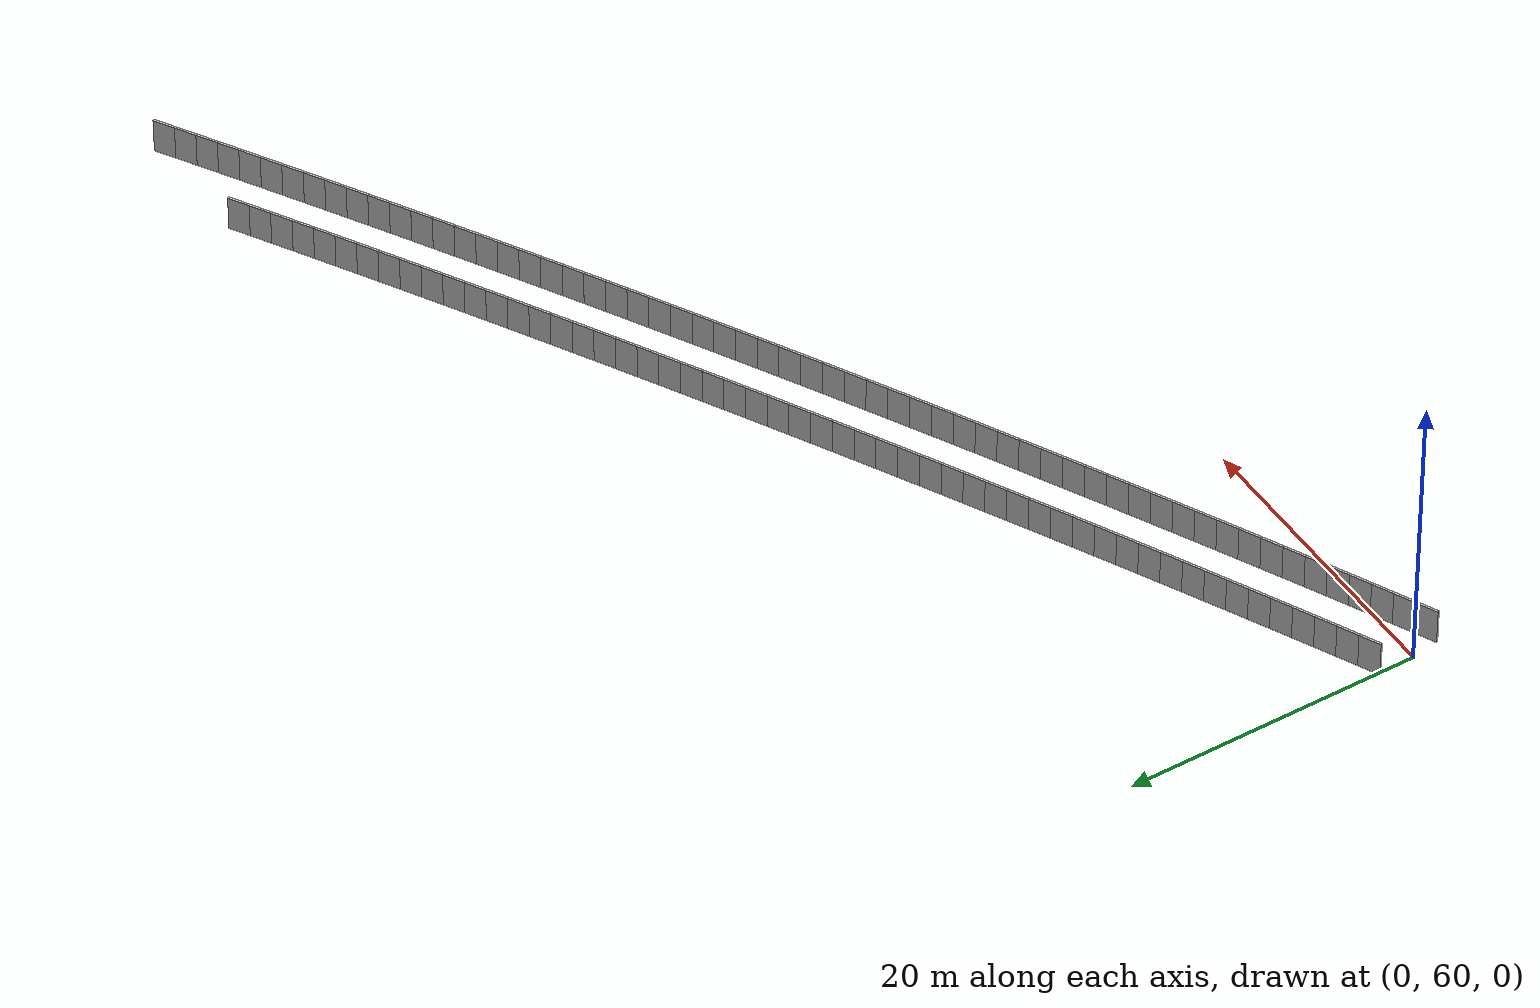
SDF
<?xml version="1.0" ?>
<sdf version="1.6">
  <model name="sps_1702">
    <pose frame="">0 0 0 0 -0 0</pose>
    <static>1</static>
    <self_collide>0</self_collide>
    <allow_auto_disable>0</allow_auto_disable>
    <link name="Wall3988">
      <kinematic>0</kinematic>
      <gravity>1</gravity>
      <self_collide>0</self_collide>
      <collision name="collision">
        <geometry>
          <box>
            <size>1.49651 0.15 2.5</size>
          </box>
        </geometry>
        <pose frame="">0 0 0 0 -0 0</pose>
      </collision>
      <visual name="visual">
        <geometry>
          <box>
            <size>1.49651 0.15 2.5</size>
          </box>
        </geometry>
        <pose frame="">0 0 0 0 -0 0</pose>
        <cast_shadows>1</cast_shadows>
        <transparency>0.0</transparency>
      </visual>
      <pose frame="">0.59185 62.7953 1.25 0 -0 0.449329</pose>
    </link>
    <link name="Wall3989">
      <kinematic>0</kinematic>
      <gravity>1</gravity>
      <self_collide>0</self_collide>
      <collision name="collision">
        <geometry>
          <box>
            <size>1.4967 0.15 2.5</size>
          </box>
        </geometry>
        <pose frame="">0 0 0 0 -0 0</pose>
      </collision>
      <visual name="visual">
        <geometry>
          <box>
            <size>1.4967 0.15 2.5</size>
          </box>
        </geometry>
        <pose frame="">0 0 0 0 -0 0</pose>
        <cast_shadows>1</cast_shadows>
        <transparency>0.0</transparency>
      </visual>
      <pose frame="">1.93944 63.4463 1.25 0 -0 0.450717</pose>
    </link>
    <link name="Wall3990">
      <kinematic>0</kinematic>
      <gravity>1</gravity>
      <self_collide>0</self_collide>
      <collision name="collision">
        <geometry>
          <box>
            <size>1.49639 0.15 2.5</size>
          </box>
        </geometry>
        <pose frame="">0 0 0 0 -0 0</pose>
      </collision>
      <visual name="visual">
        <geometry>
          <box>
            <size>1.49639 0.15 2.5</size>
          </box>
        </geometry>
        <pose frame="">0 0 0 0 -0 0</pose>
        <cast_shadows>1</cast_shadows>
        <transparency>0.0</transparency>
      </visual>
      <pose frame="">3.28597 64.0994 1.25 0 -0 0.452447</pose>
    </link>
    <link name="Wall3991">
      <kinematic>0</kinematic>
      <gravity>1</gravity>
      <self_collide>0</self_collide>
      <collision name="collision">
        <geometry>
          <box>
            <size>1.49669 0.15 2.5</size>
          </box>
        </geometry>
        <pose frame="">0 0 0 0 -0 0</pose>
      </collision>
      <visual name="visual">
        <geometry>
          <box>
            <size>1.49669 0.15 2.5</size>
          </box>
        </geometry>
        <pose frame="">0 0 0 0 -0 0</pose>
        <cast_shadows>1</cast_shadows>
        <transparency>0.0</transparency>
      </visual>
      <pose frame="">4.63137 64.7548 1.25 0 -0 0.454164</pose>
    </link>
    <link name="Wall3992">
      <kinematic>0</kinematic>
      <gravity>1</gravity>
      <self_collide>0</self_collide>
      <collision name="collision">
        <geometry>
          <box>
            <size>1.49643 0.15 2.5</size>
          </box>
        </geometry>
        <pose frame="">0 0 0 0 -0 0</pose>
      </collision>
      <visual name="visual">
        <geometry>
          <box>
            <size>1.49643 0.15 2.5</size>
          </box>
        </geometry>
        <pose frame="">0 0 0 0 -0 0</pose>
        <cast_shadows>1</cast_shadows>
        <transparency>0.0</transparency>
      </visual>
      <pose frame="">5.97576 65.4123 1.25 0 -0 0.455567</pose>
    </link>
    <link name="Wall3993">
      <kinematic>0</kinematic>
      <gravity>1</gravity>
      <self_collide>0</self_collide>
      <collision name="collision">
        <geometry>
          <box>
            <size>1.49649 0.15 2.5</size>
          </box>
        </geometry>
        <pose frame="">0 0 0 0 -0 0</pose>
      </collision>
      <visual name="visual">
        <geometry>
          <box>
            <size>1.49649 0.15 2.5</size>
          </box>
        </geometry>
        <pose frame="">0 0 0 0 -0 0</pose>
        <cast_shadows>1</cast_shadows>
        <transparency>0.0</transparency>
      </visual>
      <pose frame="">7.31905 66.0718 1.25 0 -0 0.457227</pose>
    </link>
    <link name="Wall3994">
      <kinematic>0</kinematic>
      <gravity>1</gravity>
      <self_collide>0</self_collide>
      <collision name="collision">
        <geometry>
          <box>
            <size>1.49656 0.15 2.5</size>
          </box>
        </geometry>
        <pose frame="">0 0 0 0 -0 0</pose>
      </collision>
      <visual name="visual">
        <geometry>
          <box>
            <size>1.49656 0.15 2.5</size>
          </box>
        </geometry>
        <pose frame="">0 0 0 0 -0 0</pose>
        <cast_shadows>1</cast_shadows>
        <transparency>0.0</transparency>
      </visual>
      <pose frame="">8.66134 66.7335 1.25 0 -0 0.458796</pose>
    </link>
    <link name="Wall3995">
      <kinematic>0</kinematic>
      <gravity>1</gravity>
      <self_collide>0</self_collide>
      <collision name="collision">
        <geometry>
          <box>
            <size>1.4965 0.15 2.5</size>
          </box>
        </geometry>
        <pose frame="">0 0 0 0 -0 0</pose>
      </collision>
      <visual name="visual">
        <geometry>
          <box>
            <size>1.4965 0.15 2.5</size>
          </box>
        </geometry>
        <pose frame="">0 0 0 0 -0 0</pose>
        <cast_shadows>1</cast_shadows>
        <transparency>0.0</transparency>
      </visual>
      <pose frame="">10.0026 67.3974 1.25 0 -0 0.460456</pose>
    </link>
    <link name="Wall3996">
      <kinematic>0</kinematic>
      <gravity>1</gravity>
      <self_collide>0</self_collide>
      <collision name="collision">
        <geometry>
          <box>
            <size>1.49663 0.15 2.5</size>
          </box>
        </geometry>
        <pose frame="">0 0 0 0 -0 0</pose>
      </collision>
      <visual name="visual">
        <geometry>
          <box>
            <size>1.49663 0.15 2.5</size>
          </box>
        </geometry>
        <pose frame="">0 0 0 0 -0 0</pose>
        <cast_shadows>1</cast_shadows>
        <transparency>0.0</transparency>
      </visual>
      <pose frame="">11.3428 68.0634 1.25 0 -0 0.461915</pose>
    </link>
    <link name="Wall3997">
      <kinematic>0</kinematic>
      <gravity>1</gravity>
      <self_collide>0</self_collide>
      <collision name="collision">
        <geometry>
          <box>
            <size>1.49627 0.15 2.5</size>
          </box>
        </geometry>
        <pose frame="">0 0 0 0 -0 0</pose>
      </collision>
      <visual name="visual">
        <geometry>
          <box>
            <size>1.49627 0.15 2.5</size>
          </box>
        </geometry>
        <pose frame="">0 0 0 0 -0 0</pose>
        <cast_shadows>1</cast_shadows>
        <transparency>0.0</transparency>
      </visual>
      <pose frame="">12.6818 68.7314 1.25 0 -0 0.463538</pose>
    </link>
    <link name="Wall3998">
      <kinematic>0</kinematic>
      <gravity>1</gravity>
      <self_collide>0</self_collide>
      <collision name="collision">
        <geometry>
          <box>
            <size>1.49638 0.15 2.5</size>
          </box>
        </geometry>
        <pose frame="">0 0 0 0 -0 0</pose>
      </collision>
      <visual name="visual">
        <geometry>
          <box>
            <size>1.49638 0.15 2.5</size>
          </box>
        </geometry>
        <pose frame="">0 0 0 0 -0 0</pose>
        <cast_shadows>1</cast_shadows>
        <transparency>0.0</transparency>
      </visual>
      <pose frame="">14.0197 69.4015 1.25 0 -0 0.465143</pose>
    </link>
    <link name="Wall3999">
      <kinematic>0</kinematic>
      <gravity>1</gravity>
      <self_collide>0</self_collide>
      <collision name="collision">
        <geometry>
          <box>
            <size>1.4965 0.15 2.5</size>
          </box>
        </geometry>
        <pose frame="">0 0 0 0 -0 0</pose>
      </collision>
      <visual name="visual">
        <geometry>
          <box>
            <size>1.4965 0.15 2.5</size>
          </box>
        </geometry>
        <pose frame="">0 0 0 0 -0 0</pose>
        <cast_shadows>1</cast_shadows>
        <transparency>0.0</transparency>
      </visual>
      <pose frame="">15.3567 70.0738 1.25 0 -0 0.466748</pose>
    </link>
    <link name="Wall4000">
      <kinematic>0</kinematic>
      <gravity>1</gravity>
      <self_collide>0</self_collide>
      <collision name="collision">
        <geometry>
          <box>
            <size>1.49672 0.15 2.5</size>
          </box>
        </geometry>
        <pose frame="">0 0 0 0 -0 0</pose>
      </collision>
      <visual name="visual">
        <geometry>
          <box>
            <size>1.49672 0.15 2.5</size>
          </box>
        </geometry>
        <pose frame="">0 0 0 0 -0 0</pose>
        <cast_shadows>1</cast_shadows>
        <transparency>0.0</transparency>
      </visual>
      <pose frame="">16.6926 70.7483 1.25 0 -0 0.468316</pose>
    </link>
    <link name="Wall4001">
      <kinematic>0</kinematic>
      <gravity>1</gravity>
      <self_collide>0</self_collide>
      <collision name="collision">
        <geometry>
          <box>
            <size>1.4966 0.15 2.5</size>
          </box>
        </geometry>
        <pose frame="">0 0 0 0 -0 0</pose>
      </collision>
      <visual name="visual">
        <geometry>
          <box>
            <size>1.4966 0.15 2.5</size>
          </box>
        </geometry>
        <pose frame="">0 0 0 0 -0 0</pose>
        <cast_shadows>1</cast_shadows>
        <transparency>0.0</transparency>
      </visual>
      <pose frame="">18.0276 71.4249 1.25 0 -0 0.469867</pose>
    </link>
    <link name="Wall4002">
      <kinematic>0</kinematic>
      <gravity>1</gravity>
      <self_collide>0</self_collide>
      <collision name="collision">
        <geometry>
          <box>
            <size>1.49651 0.15 2.5</size>
          </box>
        </geometry>
        <pose frame="">0 0 0 0 -0 0</pose>
      </collision>
      <visual name="visual">
        <geometry>
          <box>
            <size>1.49651 0.15 2.5</size>
          </box>
        </geometry>
        <pose frame="">0 0 0 0 -0 0</pose>
        <cast_shadows>1</cast_shadows>
        <transparency>0.0</transparency>
      </visual>
      <pose frame="">19.3614 72.1036 1.25 0 -0 0.471545</pose>
    </link>
    <link name="Wall4003">
      <kinematic>0</kinematic>
      <gravity>1</gravity>
      <self_collide>0</self_collide>
      <collision name="collision">
        <geometry>
          <box>
            <size>1.49656 0.15 2.5</size>
          </box>
        </geometry>
        <pose frame="">0 0 0 0 -0 0</pose>
      </collision>
      <visual name="visual">
        <geometry>
          <box>
            <size>1.49656 0.15 2.5</size>
          </box>
        </geometry>
        <pose frame="">0 0 0 0 -0 0</pose>
        <cast_shadows>1</cast_shadows>
        <transparency>0.0</transparency>
      </visual>
      <pose frame="">20.6941 72.7844 1.25 0 -0 0.473041</pose>
    </link>
    <link name="Wall4004">
      <kinematic>0</kinematic>
      <gravity>1</gravity>
      <self_collide>0</self_collide>
      <collision name="collision">
        <geometry>
          <box>
            <size>1.49661 0.15 2.5</size>
          </box>
        </geometry>
        <pose frame="">0 0 0 0 -0 0</pose>
      </collision>
      <visual name="visual">
        <geometry>
          <box>
            <size>1.49661 0.15 2.5</size>
          </box>
        </geometry>
        <pose frame="">0 0 0 0 -0 0</pose>
        <cast_shadows>1</cast_shadows>
        <transparency>0.0</transparency>
      </visual>
      <pose frame="">22.0258 73.4673 1.25 0 -0 0.474627</pose>
    </link>
    <link name="Wall4005">
      <kinematic>0</kinematic>
      <gravity>1</gravity>
      <self_collide>0</self_collide>
      <collision name="collision">
        <geometry>
          <box>
            <size>1.49636 0.15 2.5</size>
          </box>
        </geometry>
        <pose frame="">0 0 0 0 -0 0</pose>
      </collision>
      <visual name="visual">
        <geometry>
          <box>
            <size>1.49636 0.15 2.5</size>
          </box>
        </geometry>
        <pose frame="">0 0 0 0 -0 0</pose>
        <cast_shadows>1</cast_shadows>
        <transparency>0.0</transparency>
      </visual>
      <pose frame="">23.3563 74.1523 1.25 0 -0 0.476271</pose>
    </link>
    <link name="Wall4006">
      <kinematic>0</kinematic>
      <gravity>1</gravity>
      <self_collide>0</self_collide>
      <collision name="collision">
        <geometry>
          <box>
            <size>1.49658 0.15 2.5</size>
          </box>
        </geometry>
        <pose frame="">0 0 0 0 -0 0</pose>
      </collision>
      <visual name="visual">
        <geometry>
          <box>
            <size>1.49658 0.15 2.5</size>
          </box>
        </geometry>
        <pose frame="">0 0 0 0 -0 0</pose>
        <cast_shadows>1</cast_shadows>
        <transparency>0.0</transparency>
      </visual>
      <pose frame="">24.6858 74.8394 1.25 0 -0 0.477801</pose>
    </link>
    <link name="Wall4007">
      <kinematic>0</kinematic>
      <gravity>1</gravity>
      <self_collide>0</self_collide>
      <collision name="collision">
        <geometry>
          <box>
            <size>1.49676 0.15 2.5</size>
          </box>
        </geometry>
        <pose frame="">0 0 0 0 -0 0</pose>
      </collision>
      <visual name="visual">
        <geometry>
          <box>
            <size>1.49676 0.15 2.5</size>
          </box>
        </geometry>
        <pose frame="">0 0 0 0 -0 0</pose>
        <cast_shadows>1</cast_shadows>
        <transparency>0.0</transparency>
      </visual>
      <pose frame="">26.0142 75.5287 1.25 0 -0 0.479441</pose>
    </link>
    <link name="Wall4008">
      <kinematic>0</kinematic>
      <gravity>1</gravity>
      <self_collide>0</self_collide>
      <collision name="collision">
        <geometry>
          <box>
            <size>1.49642 0.15 2.5</size>
          </box>
        </geometry>
        <pose frame="">0 0 0 0 -0 0</pose>
      </collision>
      <visual name="visual">
        <geometry>
          <box>
            <size>1.49642 0.15 2.5</size>
          </box>
        </geometry>
        <pose frame="">0 0 0 0 -0 0</pose>
        <cast_shadows>1</cast_shadows>
        <transparency>0.0</transparency>
      </visual>
      <pose frame="">27.3415 76.2201 1.25 0 -0 0.481032</pose>
    </link>
    <link name="Wall4009">
      <kinematic>0</kinematic>
      <gravity>1</gravity>
      <self_collide>0</self_collide>
      <collision name="collision">
        <geometry>
          <box>
            <size>1.49648 0.15 2.5</size>
          </box>
        </geometry>
        <pose frame="">0 0 0 0 -0 0</pose>
      </collision>
      <visual name="visual">
        <geometry>
          <box>
            <size>1.49648 0.15 2.5</size>
          </box>
        </geometry>
        <pose frame="">0 0 0 0 -0 0</pose>
        <cast_shadows>1</cast_shadows>
        <transparency>0.0</transparency>
      </visual>
      <pose frame="">28.6677 76.9135 1.25 0 -0 0.482527</pose>
    </link>
    <link name="Wall4010">
      <kinematic>0</kinematic>
      <gravity>1</gravity>
      <self_collide>0</self_collide>
      <collision name="collision">
        <geometry>
          <box>
            <size>1.49659 0.15 2.5</size>
          </box>
        </geometry>
        <pose frame="">0 0 0 0 -0 0</pose>
      </collision>
      <visual name="visual">
        <geometry>
          <box>
            <size>1.49659 0.15 2.5</size>
          </box>
        </geometry>
        <pose frame="">0 0 0 0 -0 0</pose>
        <cast_shadows>1</cast_shadows>
        <transparency>0.0</transparency>
      </visual>
      <pose frame="">29.9928 77.609 1.25 0 -0 0.484149</pose>
    </link>
    <link name="Wall4011">
      <kinematic>0</kinematic>
      <gravity>1</gravity>
      <self_collide>0</self_collide>
      <collision name="collision">
        <geometry>
          <box>
            <size>1.4965 0.15 2.5</size>
          </box>
        </geometry>
        <pose frame="">0 0 0 0 -0 0</pose>
      </collision>
      <visual name="visual">
        <geometry>
          <box>
            <size>1.4965 0.15 2.5</size>
          </box>
        </geometry>
        <pose frame="">0 0 0 0 -0 0</pose>
        <cast_shadows>1</cast_shadows>
        <transparency>0.0</transparency>
      </visual>
      <pose frame="">31.3168 78.3066 1.25 0 -0 0.485701</pose>
    </link>
    <link name="Wall4012">
      <kinematic>0</kinematic>
      <gravity>1</gravity>
      <self_collide>0</self_collide>
      <collision name="collision">
        <geometry>
          <box>
            <size>1.49645 0.15 2.5</size>
          </box>
        </geometry>
        <pose frame="">0 0 0 0 -0 0</pose>
      </collision>
      <visual name="visual">
        <geometry>
          <box>
            <size>1.49645 0.15 2.5</size>
          </box>
        </geometry>
        <pose frame="">0 0 0 0 -0 0</pose>
        <cast_shadows>1</cast_shadows>
        <transparency>0.0</transparency>
      </visual>
      <pose frame="">32.6396 79.0063 1.25 0 -0 0.487381</pose>
    </link>
    <link name="Wall4013">
      <kinematic>0</kinematic>
      <gravity>1</gravity>
      <self_collide>0</self_collide>
      <collision name="collision">
        <geometry>
          <box>
            <size>1.49661 0.15 2.5</size>
          </box>
        </geometry>
        <pose frame="">0 0 0 0 -0 0</pose>
      </collision>
      <visual name="visual">
        <geometry>
          <box>
            <size>1.49661 0.15 2.5</size>
          </box>
        </geometry>
        <pose frame="">0 0 0 0 -0 0</pose>
        <cast_shadows>1</cast_shadows>
        <transparency>0.0</transparency>
      </visual>
      <pose frame="">33.9614 79.7081 1.25 0 -0 0.488801</pose>
    </link>
    <link name="Wall4014">
      <kinematic>0</kinematic>
      <gravity>1</gravity>
      <self_collide>0</self_collide>
      <collision name="collision">
        <geometry>
          <box>
            <size>1.49649 0.15 2.5</size>
          </box>
        </geometry>
        <pose frame="">0 0 0 0 -0 0</pose>
      </collision>
      <visual name="visual">
        <geometry>
          <box>
            <size>1.49649 0.15 2.5</size>
          </box>
        </geometry>
        <pose frame="">0 0 0 0 -0 0</pose>
        <cast_shadows>1</cast_shadows>
        <transparency>0.0</transparency>
      </visual>
      <pose frame="">35.282 80.412 1.25 0 -0 0.490555</pose>
    </link>
    <link name="Wall4015">
      <kinematic>0</kinematic>
      <gravity>1</gravity>
      <self_collide>0</self_collide>
      <collision name="collision">
        <geometry>
          <box>
            <size>1.49657 0.15 2.5</size>
          </box>
        </geometry>
        <pose frame="">0 0 0 0 -0 0</pose>
      </collision>
      <visual name="visual">
        <geometry>
          <box>
            <size>1.49657 0.15 2.5</size>
          </box>
        </geometry>
        <pose frame="">0 0 0 0 -0 0</pose>
        <cast_shadows>1</cast_shadows>
        <transparency>0.0</transparency>
      </visual>
      <pose frame="">36.6016 81.118 1.25 0 -0 0.492049</pose>
    </link>
    <link name="Wall4016">
      <kinematic>0</kinematic>
      <gravity>1</gravity>
      <self_collide>0</self_collide>
      <collision name="collision">
        <geometry>
          <box>
            <size>1.49651 0.15 2.5</size>
          </box>
        </geometry>
        <pose frame="">0 0 0 0 -0 0</pose>
      </collision>
      <visual name="visual">
        <geometry>
          <box>
            <size>1.49651 0.15 2.5</size>
          </box>
        </geometry>
        <pose frame="">0 0 0 0 -0 0</pose>
        <cast_shadows>1</cast_shadows>
        <transparency>0.0</transparency>
      </visual>
      <pose frame="">37.92 81.8261 1.25 0 -0 0.493693</pose>
    </link>
    <link name="Wall4017">
      <kinematic>0</kinematic>
      <gravity>1</gravity>
      <self_collide>0</self_collide>
      <collision name="collision">
        <geometry>
          <box>
            <size>1.49674 0.15 2.5</size>
          </box>
        </geometry>
        <pose frame="">0 0 0 0 -0 0</pose>
      </collision>
      <visual name="visual">
        <geometry>
          <box>
            <size>1.49674 0.15 2.5</size>
          </box>
        </geometry>
        <pose frame="">0 0 0 0 -0 0</pose>
        <cast_shadows>1</cast_shadows>
        <transparency>0.0</transparency>
      </visual>
      <pose frame="">39.2374 82.5363 1.25 0 -0 0.495184</pose>
    </link>
    <link name="Wall4018">
      <kinematic>0</kinematic>
      <gravity>1</gravity>
      <self_collide>0</self_collide>
      <collision name="collision">
        <geometry>
          <box>
            <size>1.49658 0.15 2.5</size>
          </box>
        </geometry>
        <pose frame="">0 0 0 0 -0 0</pose>
      </collision>
      <visual name="visual">
        <geometry>
          <box>
            <size>1.49658 0.15 2.5</size>
          </box>
        </geometry>
        <pose frame="">0 0 0 0 -0 0</pose>
        <cast_shadows>1</cast_shadows>
        <transparency>0.0</transparency>
      </visual>
      <pose frame="">40.5536 83.2486 1.25 0 -0 0.496867</pose>
    </link>
    <link name="Wall4019">
      <kinematic>0</kinematic>
      <gravity>1</gravity>
      <self_collide>0</self_collide>
      <collision name="collision">
        <geometry>
          <box>
            <size>1.49647 0.15 2.5</size>
          </box>
        </geometry>
        <pose frame="">0 0 0 0 -0 0</pose>
      </collision>
      <visual name="visual">
        <geometry>
          <box>
            <size>1.49647 0.15 2.5</size>
          </box>
        </geometry>
        <pose frame="">0 0 0 0 -0 0</pose>
        <cast_shadows>1</cast_shadows>
        <transparency>0.0</transparency>
      </visual>
      <pose frame="">41.8686 83.963 1.25 0 -0 0.498439</pose>
    </link>
    <link name="Wall4020">
      <kinematic>0</kinematic>
      <gravity>1</gravity>
      <self_collide>0</self_collide>
      <collision name="collision">
        <geometry>
          <box>
            <size>1.49641 0.15 2.5</size>
          </box>
        </geometry>
        <pose frame="">0 0 0 0 -0 0</pose>
      </collision>
      <visual name="visual">
        <geometry>
          <box>
            <size>1.49641 0.15 2.5</size>
          </box>
        </geometry>
        <pose frame="">0 0 0 0 -0 0</pose>
        <cast_shadows>1</cast_shadows>
        <transparency>0.0</transparency>
      </visual>
      <pose frame="">43.1825 84.6794 1.25 0 -0 0.499991</pose>
    </link>
    <link name="Wall4021">
      <kinematic>0</kinematic>
      <gravity>1</gravity>
      <self_collide>0</self_collide>
      <collision name="collision">
        <geometry>
          <box>
            <size>1.49656 0.15 2.5</size>
          </box>
        </geometry>
        <pose frame="">0 0 0 0 -0 0</pose>
      </collision>
      <visual name="visual">
        <geometry>
          <box>
            <size>1.49656 0.15 2.5</size>
          </box>
        </geometry>
        <pose frame="">0 0 0 0 -0 0</pose>
        <cast_shadows>1</cast_shadows>
        <transparency>0.0</transparency>
      </visual>
      <pose frame="">44.4952 85.3979 1.25 0 -0 0.501612</pose>
    </link>
    <link name="Wall4022">
      <kinematic>0</kinematic>
      <gravity>1</gravity>
      <self_collide>0</self_collide>
      <collision name="collision">
        <geometry>
          <box>
            <size>1.49655 0.15 2.5</size>
          </box>
        </geometry>
        <pose frame="">0 0 0 0 -0 0</pose>
      </collision>
      <visual name="visual">
        <geometry>
          <box>
            <size>1.49655 0.15 2.5</size>
          </box>
        </geometry>
        <pose frame="">0 0 0 0 -0 0</pose>
        <cast_shadows>1</cast_shadows>
        <transparency>0.0</transparency>
      </visual>
      <pose frame="">45.8068 86.1186 1.25 0 -0 0.503292</pose>
    </link>
    <link name="Wall4023">
      <kinematic>0</kinematic>
      <gravity>1</gravity>
      <self_collide>0</self_collide>
      <collision name="collision">
        <geometry>
          <box>
            <size>1.49639 0.15 2.5</size>
          </box>
        </geometry>
        <pose frame="">0 0 0 0 -0 0</pose>
      </collision>
      <visual name="visual">
        <geometry>
          <box>
            <size>1.49639 0.15 2.5</size>
          </box>
        </geometry>
        <pose frame="">0 0 0 0 -0 0</pose>
        <cast_shadows>1</cast_shadows>
        <transparency>0.0</transparency>
      </visual>
      <pose frame="">47.1171 86.8413 1.25 0 -0 0.504702</pose>
    </link>
    <link name="Wall4024">
      <kinematic>0</kinematic>
      <gravity>1</gravity>
      <self_collide>0</self_collide>
      <collision name="collision">
        <geometry>
          <box>
            <size>1.49657 0.15 2.5</size>
          </box>
        </geometry>
        <pose frame="">0 0 0 0 -0 0</pose>
      </collision>
      <visual name="visual">
        <geometry>
          <box>
            <size>1.49657 0.15 2.5</size>
          </box>
        </geometry>
        <pose frame="">0 0 0 0 -0 0</pose>
        <cast_shadows>1</cast_shadows>
        <transparency>0.0</transparency>
      </visual>
      <pose frame="">48.4264 87.566 1.25 0 -0 0.506358</pose>
    </link>
    <link name="Wall4025">
      <kinematic>0</kinematic>
      <gravity>1</gravity>
      <self_collide>0</self_collide>
      <collision name="collision">
        <geometry>
          <box>
            <size>1.49651 0.15 2.5</size>
          </box>
        </geometry>
        <pose frame="">0 0 0 0 -0 0</pose>
      </collision>
      <visual name="visual">
        <geometry>
          <box>
            <size>1.49651 0.15 2.5</size>
          </box>
        </geometry>
        <pose frame="">0 0 0 0 -0 0</pose>
        <cast_shadows>1</cast_shadows>
        <transparency>0.0</transparency>
      </visual>
      <pose frame="">49.7346 88.2928 1.25 0 -0 0.507875</pose>
    </link>
    <link name="Wall4026">
      <kinematic>0</kinematic>
      <gravity>1</gravity>
      <self_collide>0</self_collide>
      <collision name="collision">
        <geometry>
          <box>
            <size>1.49667 0.15 2.5</size>
          </box>
        </geometry>
        <pose frame="">0 0 0 0 -0 0</pose>
      </collision>
      <visual name="visual">
        <geometry>
          <box>
            <size>1.49667 0.15 2.5</size>
          </box>
        </geometry>
        <pose frame="">0 0 0 0 -0 0</pose>
        <cast_shadows>1</cast_shadows>
        <transparency>0.0</transparency>
      </visual>
      <pose frame="">51.0417 89.0217 1.25 0 -0 0.509495</pose>
    </link>
    <link name="Wall4027">
      <kinematic>0</kinematic>
      <gravity>1</gravity>
      <self_collide>0</self_collide>
      <collision name="collision">
        <geometry>
          <box>
            <size>1.49648 0.15 2.5</size>
          </box>
        </geometry>
        <pose frame="">0 0 0 0 -0 0</pose>
      </collision>
      <visual name="visual">
        <geometry>
          <box>
            <size>1.49648 0.15 2.5</size>
          </box>
        </geometry>
        <pose frame="">0 0 0 0 -0 0</pose>
        <cast_shadows>1</cast_shadows>
        <transparency>0.0</transparency>
      </visual>
      <pose frame="">52.3476 89.7527 1.25 0 -0 0.511108</pose>
    </link>
    <link name="Wall4028">
      <kinematic>0</kinematic>
      <gravity>1</gravity>
      <self_collide>0</self_collide>
      <collision name="collision">
        <geometry>
          <box>
            <size>1.49656 0.15 2.5</size>
          </box>
        </geometry>
        <pose frame="">0 0 0 0 -0 0</pose>
      </collision>
      <visual name="visual">
        <geometry>
          <box>
            <size>1.49656 0.15 2.5</size>
          </box>
        </geometry>
        <pose frame="">0 0 0 0 -0 0</pose>
        <cast_shadows>1</cast_shadows>
        <transparency>0.0</transparency>
      </visual>
      <pose frame="">53.6524 90.4857 1.25 0 -0 0.512621</pose>
    </link>
    <link name="Wall4029">
      <kinematic>0</kinematic>
      <gravity>1</gravity>
      <self_collide>0</self_collide>
      <collision name="collision">
        <geometry>
          <box>
            <size>1.49658 0.15 2.5</size>
          </box>
        </geometry>
        <pose frame="">0 0 0 0 -0 0</pose>
      </collision>
      <visual name="visual">
        <geometry>
          <box>
            <size>1.49658 0.15 2.5</size>
          </box>
        </geometry>
        <pose frame="">0 0 0 0 -0 0</pose>
        <cast_shadows>1</cast_shadows>
        <transparency>0.0</transparency>
      </visual>
      <pose frame="">54.956 91.2208 1.25 0 -0 0.5143</pose>
    </link>
    <link name="Wall4030">
      <kinematic>0</kinematic>
      <gravity>1</gravity>
      <self_collide>0</self_collide>
      <collision name="collision">
        <geometry>
          <box>
            <size>1.49656 0.15 2.5</size>
          </box>
        </geometry>
        <pose frame="">0 0 0 0 -0 0</pose>
      </collision>
      <visual name="visual">
        <geometry>
          <box>
            <size>1.49656 0.15 2.5</size>
          </box>
        </geometry>
        <pose frame="">0 0 0 0 -0 0</pose>
        <cast_shadows>1</cast_shadows>
        <transparency>0.0</transparency>
      </visual>
      <pose frame="">56.2584 91.958 1.25 0 -0 0.515853</pose>
    </link>
    <link name="Wall4031">
      <kinematic>0</kinematic>
      <gravity>1</gravity>
      <self_collide>0</self_collide>
      <collision name="collision">
        <geometry>
          <box>
            <size>1.49647 0.15 2.5</size>
          </box>
        </geometry>
        <pose frame="">0 0 0 0 -0 0</pose>
      </collision>
      <visual name="visual">
        <geometry>
          <box>
            <size>1.49647 0.15 2.5</size>
          </box>
        </geometry>
        <pose frame="">0 0 0 0 -0 0</pose>
        <cast_shadows>1</cast_shadows>
        <transparency>0.0</transparency>
      </visual>
      <pose frame="">57.5596 92.6972 1.25 0 -0 0.517391</pose>
    </link>
    <link name="Wall4032">
      <kinematic>0</kinematic>
      <gravity>1</gravity>
      <self_collide>0</self_collide>
      <collision name="collision">
        <geometry>
          <box>
            <size>1.49652 0.15 2.5</size>
          </box>
        </geometry>
        <pose frame="">0 0 0 0 -0 0</pose>
      </collision>
      <visual name="visual">
        <geometry>
          <box>
            <size>1.49652 0.15 2.5</size>
          </box>
        </geometry>
        <pose frame="">0 0 0 0 -0 0</pose>
        <cast_shadows>1</cast_shadows>
        <transparency>0.0</transparency>
      </visual>
      <pose frame="">58.8595 93.4385 1.25 0 -0 0.519106</pose>
    </link>
    <link name="Wall4033">
      <kinematic>0</kinematic>
      <gravity>1</gravity>
      <self_collide>0</self_collide>
      <collision name="collision">
        <geometry>
          <box>
            <size>1.49649 0.15 2.5</size>
          </box>
        </geometry>
        <pose frame="">0 0 0 0 -0 0</pose>
      </collision>
      <visual name="visual">
        <geometry>
          <box>
            <size>1.49649 0.15 2.5</size>
          </box>
        </geometry>
        <pose frame="">0 0 0 0 -0 0</pose>
        <cast_shadows>1</cast_shadows>
        <transparency>0.0</transparency>
      </visual>
      <pose frame="">60.1583 94.1819 1.25 0 -0 0.520623</pose>
    </link>
    <link name="Wall4034">
      <kinematic>0</kinematic>
      <gravity>1</gravity>
      <self_collide>0</self_collide>
      <collision name="collision">
        <geometry>
          <box>
            <size>1.49659 0.15 2.5</size>
          </box>
        </geometry>
        <pose frame="">0 0 0 0 -0 0</pose>
      </collision>
      <visual name="visual">
        <geometry>
          <box>
            <size>1.49659 0.15 2.5</size>
          </box>
        </geometry>
        <pose frame="">0 0 0 0 -0 0</pose>
        <cast_shadows>1</cast_shadows>
        <transparency>0.0</transparency>
      </visual>
      <pose frame="">61.456 94.9273 1.25 0 -0 0.522136</pose>
    </link>
    <link name="Wall4035">
      <kinematic>0</kinematic>
      <gravity>1</gravity>
      <self_collide>0</self_collide>
      <collision name="collision">
        <geometry>
          <box>
            <size>1.49659 0.15 2.5</size>
          </box>
        </geometry>
        <pose frame="">0 0 0 0 -0 0</pose>
      </collision>
      <visual name="visual">
        <geometry>
          <box>
            <size>1.49659 0.15 2.5</size>
          </box>
        </geometry>
        <pose frame="">0 0 0 0 -0 0</pose>
        <cast_shadows>1</cast_shadows>
        <transparency>0.0</transparency>
      </visual>
      <pose frame="">62.7526 95.6747 1.25 0 -0 0.523689</pose>
    </link>
    <link name="Wall4036">
      <kinematic>0</kinematic>
      <gravity>1</gravity>
      <self_collide>0</self_collide>
      <collision name="collision">
        <geometry>
          <box>
            <size>1.49648 0.15 2.5</size>
          </box>
        </geometry>
        <pose frame="">0 0 0 0 -0 0</pose>
      </collision>
      <visual name="visual">
        <geometry>
          <box>
            <size>1.49648 0.15 2.5</size>
          </box>
        </geometry>
        <pose frame="">0 0 0 0 -0 0</pose>
        <cast_shadows>1</cast_shadows>
        <transparency>0.0</transparency>
      </visual>
      <pose frame="">64.048 96.4242 1.25 0 -0 0.525429</pose>
    </link>
    <link name="Wall4037">
      <kinematic>0</kinematic>
      <gravity>1</gravity>
      <self_collide>0</self_collide>
      <collision name="collision">
        <geometry>
          <box>
            <size>1.4964 0.15 2.5</size>
          </box>
        </geometry>
        <pose frame="">0 0 0 0 -0 0</pose>
      </collision>
      <visual name="visual">
        <geometry>
          <box>
            <size>1.4964 0.15 2.5</size>
          </box>
        </geometry>
        <pose frame="">0 0 0 0 -0 0</pose>
        <cast_shadows>1</cast_shadows>
        <transparency>0.0</transparency>
      </visual>
      <pose frame="">65.342 97.1758 1.25 0 -0 0.526968</pose>
    </link>
    <link name="Wall4038">
      <kinematic>0</kinematic>
      <gravity>1</gravity>
      <self_collide>0</self_collide>
      <collision name="collision">
        <geometry>
          <box>
            <size>1.49643 0.15 2.5</size>
          </box>
        </geometry>
        <pose frame="">0 0 0 0 -0 0</pose>
      </collision>
      <visual name="visual">
        <geometry>
          <box>
            <size>1.49643 0.15 2.5</size>
          </box>
        </geometry>
        <pose frame="">0 0 0 0 -0 0</pose>
        <cast_shadows>1</cast_shadows>
        <transparency>0.0</transparency>
      </visual>
      <pose frame="">66.6348 97.9293 1.25 0 -0 0.528374</pose>
    </link>
    <link name="Wall4039">
      <kinematic>0</kinematic>
      <gravity>1</gravity>
      <self_collide>0</self_collide>
      <collision name="collision">
        <geometry>
          <box>
            <size>1.49666 0.15 2.5</size>
          </box>
        </geometry>
        <pose frame="">0 0 0 0 -0 0</pose>
      </collision>
      <visual name="visual">
        <geometry>
          <box>
            <size>1.49666 0.15 2.5</size>
          </box>
        </geometry>
        <pose frame="">0 0 0 0 -0 0</pose>
        <cast_shadows>1</cast_shadows>
        <transparency>0.0</transparency>
      </visual>
      <pose frame="">67.9266 98.6849 1.25 0 -0 0.530173</pose>
    </link>
    <link name="Wall4040">
      <kinematic>0</kinematic>
      <gravity>1</gravity>
      <self_collide>0</self_collide>
      <collision name="collision">
        <geometry>
          <box>
            <size>1.49656 0.15 2.5</size>
          </box>
        </geometry>
        <pose frame="">0 0 0 0 -0 0</pose>
      </collision>
      <visual name="visual">
        <geometry>
          <box>
            <size>1.49656 0.15 2.5</size>
          </box>
        </geometry>
        <pose frame="">0 0 0 0 -0 0</pose>
        <cast_shadows>1</cast_shadows>
        <transparency>0.0</transparency>
      </visual>
      <pose frame="">69.2172 99.4426 1.25 0 -0 0.531586</pose>
    </link>
    <link name="Wall7762">
      <kinematic>0</kinematic>
      <gravity>1</gravity>
      <self_collide>0</self_collide>
      <collision name="collision">
        <geometry>
          <box>
            <size>1.50307 0.15 2.5</size>
          </box>
        </geometry>
        <pose frame="">0 0 0 0 -0 0</pose>
      </collision>
      <visual name="visual">
        <geometry>
          <box>
            <size>1.50307 0.15 2.5</size>
          </box>
        </geometry>
        <pose frame="">0 0 0 0 -0 0</pose>
        <cast_shadows>1</cast_shadows>
        <transparency>0.0</transparency>
      </visual>
      <pose frame="">1.03774 58.4148 1.25 0 -0 0.44763</pose>
    </link>
    <link name="Wall7763">
      <kinematic>0</kinematic>
      <gravity>1</gravity>
      <self_collide>0</self_collide>
      <collision name="collision">
        <geometry>
          <box>
            <size>1.50317 0.15 2.5</size>
          </box>
        </geometry>
        <pose frame="">0 0 0 0 -0 0</pose>
      </collision>
      <visual name="visual">
        <geometry>
          <box>
            <size>1.50317 0.15 2.5</size>
          </box>
        </geometry>
        <pose frame="">0 0 0 0 -0 0</pose>
        <cast_shadows>1</cast_shadows>
        <transparency>0.0</transparency>
      </visual>
      <pose frame="">2.39223 59.0665 1.25 0 -0 0.449265</pose>
    </link>
    <link name="Wall7764">
      <kinematic>0</kinematic>
      <gravity>1</gravity>
      <self_collide>0</self_collide>
      <collision name="collision">
        <geometry>
          <box>
            <size>1.50305 0.15 2.5</size>
          </box>
        </geometry>
        <pose frame="">0 0 0 0 -0 0</pose>
      </collision>
      <visual name="visual">
        <geometry>
          <box>
            <size>1.50305 0.15 2.5</size>
          </box>
        </geometry>
        <pose frame="">0 0 0 0 -0 0</pose>
        <cast_shadows>1</cast_shadows>
        <transparency>0.0</transparency>
      </visual>
      <pose frame="">3.74566 59.7204 1.25 0 -0 0.450881</pose>
    </link>
    <link name="Wall7765">
      <kinematic>0</kinematic>
      <gravity>1</gravity>
      <self_collide>0</self_collide>
      <collision name="collision">
        <geometry>
          <box>
            <size>1.50297 0.15 2.5</size>
          </box>
        </geometry>
        <pose frame="">0 0 0 0 -0 0</pose>
      </collision>
      <visual name="visual">
        <geometry>
          <box>
            <size>1.50297 0.15 2.5</size>
          </box>
        </geometry>
        <pose frame="">0 0 0 0 -0 0</pose>
        <cast_shadows>1</cast_shadows>
        <transparency>0.0</transparency>
      </visual>
      <pose frame="">5.09795 60.3764 1.25 0 -0 0.452442</pose>
    </link>
    <link name="Wall7766">
      <kinematic>0</kinematic>
      <gravity>1</gravity>
      <self_collide>0</self_collide>
      <collision name="collision">
        <geometry>
          <box>
            <size>1.50316 0.15 2.5</size>
          </box>
        </geometry>
        <pose frame="">0 0 0 0 -0 0</pose>
      </collision>
      <visual name="visual">
        <geometry>
          <box>
            <size>1.50316 0.15 2.5</size>
          </box>
        </geometry>
        <pose frame="">0 0 0 0 -0 0</pose>
        <cast_shadows>1</cast_shadows>
        <transparency>0.0</transparency>
      </visual>
      <pose frame="">6.44924 61.0346 1.25 0 -0 0.454096</pose>
    </link>
    <link name="Wall7767">
      <kinematic>0</kinematic>
      <gravity>1</gravity>
      <self_collide>0</self_collide>
      <collision name="collision">
        <geometry>
          <box>
            <size>1.50298 0.15 2.5</size>
          </box>
        </geometry>
        <pose frame="">0 0 0 0 -0 0</pose>
      </collision>
      <visual name="visual">
        <geometry>
          <box>
            <size>1.50298 0.15 2.5</size>
          </box>
        </geometry>
        <pose frame="">0 0 0 0 -0 0</pose>
        <cast_shadows>1</cast_shadows>
        <transparency>0.0</transparency>
      </visual>
      <pose frame="">7.79946 61.695 1.25 0 -0 0.455693</pose>
    </link>
    <link name="Wall7768">
      <kinematic>0</kinematic>
      <gravity>1</gravity>
      <self_collide>0</self_collide>
      <collision name="collision">
        <geometry>
          <box>
            <size>1.50321 0.15 2.5</size>
          </box>
        </geometry>
        <pose frame="">0 0 0 0 -0 0</pose>
      </collision>
      <visual name="visual">
        <geometry>
          <box>
            <size>1.50321 0.15 2.5</size>
          </box>
        </geometry>
        <pose frame="">0 0 0 0 -0 0</pose>
        <cast_shadows>1</cast_shadows>
        <transparency>0.0</transparency>
      </visual>
      <pose frame="">9.14867 62.3575 1.25 0 -0 0.457201</pose>
    </link>
    <link name="Wall7769">
      <kinematic>0</kinematic>
      <gravity>1</gravity>
      <self_collide>0</self_collide>
      <collision name="collision">
        <geometry>
          <box>
            <size>1.503 0.15 2.5</size>
          </box>
        </geometry>
        <pose frame="">0 0 0 0 -0 0</pose>
      </collision>
      <visual name="visual">
        <geometry>
          <box>
            <size>1.503 0.15 2.5</size>
          </box>
        </geometry>
        <pose frame="">0 0 0 0 -0 0</pose>
        <cast_shadows>1</cast_shadows>
        <transparency>0.0</transparency>
      </visual>
      <pose frame="">10.4969 63.0221 1.25 0 -0 0.458762</pose>
    </link>
    <link name="Wall7770">
      <kinematic>0</kinematic>
      <gravity>1</gravity>
      <self_collide>0</self_collide>
      <collision name="collision">
        <geometry>
          <box>
            <size>1.50316 0.15 2.5</size>
          </box>
        </geometry>
        <pose frame="">0 0 0 0 -0 0</pose>
      </collision>
      <visual name="visual">
        <geometry>
          <box>
            <size>1.50316 0.15 2.5</size>
          </box>
        </geometry>
        <pose frame="">0 0 0 0 -0 0</pose>
        <cast_shadows>1</cast_shadows>
        <transparency>0.0</transparency>
      </visual>
      <pose frame="">11.844 63.6889 1.25 0 -0 0.460524</pose>
    </link>
    <link name="Wall7771">
      <kinematic>0</kinematic>
      <gravity>1</gravity>
      <self_collide>0</self_collide>
      <collision name="collision">
        <geometry>
          <box>
            <size>1.50299 0.15 2.5</size>
          </box>
        </geometry>
        <pose frame="">0 0 0 0 -0 0</pose>
      </collision>
      <visual name="visual">
        <geometry>
          <box>
            <size>1.50299 0.15 2.5</size>
          </box>
        </geometry>
        <pose frame="">0 0 0 0 -0 0</pose>
        <cast_shadows>1</cast_shadows>
        <transparency>0.0</transparency>
      </visual>
      <pose frame="">13.1899 64.3579 1.25 0 -0 0.462031</pose>
    </link>
    <link name="Wall7772">
      <kinematic>0</kinematic>
      <gravity>1</gravity>
      <self_collide>0</self_collide>
      <collision name="collision">
        <geometry>
          <box>
            <size>1.50301 0.15 2.5</size>
          </box>
        </geometry>
        <pose frame="">0 0 0 0 -0 0</pose>
      </collision>
      <visual name="visual">
        <geometry>
          <box>
            <size>1.50301 0.15 2.5</size>
          </box>
        </geometry>
        <pose frame="">0 0 0 0 -0 0</pose>
        <cast_shadows>1</cast_shadows>
        <transparency>0.0</transparency>
      </visual>
      <pose frame="">14.5348 65.0289 1.25 0 -0 0.46352</pose>
    </link>
    <link name="Wall7773">
      <kinematic>0</kinematic>
      <gravity>1</gravity>
      <self_collide>0</self_collide>
      <collision name="collision">
        <geometry>
          <box>
            <size>1.50307 0.15 2.5</size>
          </box>
        </geometry>
        <pose frame="">0 0 0 0 -0 0</pose>
      </collision>
      <visual name="visual">
        <geometry>
          <box>
            <size>1.50307 0.15 2.5</size>
          </box>
        </geometry>
        <pose frame="">0 0 0 0 -0 0</pose>
        <cast_shadows>1</cast_shadows>
        <transparency>0.0</transparency>
      </visual>
      <pose frame="">15.8787 65.702 1.25 0 -0 0.465137</pose>
    </link>
    <link name="Wall7774">
      <kinematic>0</kinematic>
      <gravity>1</gravity>
      <self_collide>0</self_collide>
      <collision name="collision">
        <geometry>
          <box>
            <size>1.50318 0.15 2.5</size>
          </box>
        </geometry>
        <pose frame="">0 0 0 0 -0 0</pose>
      </collision>
      <visual name="visual">
        <geometry>
          <box>
            <size>1.50318 0.15 2.5</size>
          </box>
        </geometry>
        <pose frame="">0 0 0 0 -0 0</pose>
        <cast_shadows>1</cast_shadows>
        <transparency>0.0</transparency>
      </visual>
      <pose frame="">17.2216 66.3773 1.25 0 -0 0.466735</pose>
    </link>
    <link name="Wall7775">
      <kinematic>0</kinematic>
      <gravity>1</gravity>
      <self_collide>0</self_collide>
      <collision name="collision">
        <geometry>
          <box>
            <size>1.503 0.15 2.5</size>
          </box>
        </geometry>
        <pose frame="">0 0 0 0 -0 0</pose>
      </collision>
      <visual name="visual">
        <geometry>
          <box>
            <size>1.503 0.15 2.5</size>
          </box>
        </geometry>
        <pose frame="">0 0 0 0 -0 0</pose>
        <cast_shadows>1</cast_shadows>
        <transparency>0.0</transparency>
      </visual>
      <pose frame="">18.5634 67.0547 1.25 0 -0 0.468297</pose>
    </link>
    <link name="Wall7776">
      <kinematic>0</kinematic>
      <gravity>1</gravity>
      <self_collide>0</self_collide>
      <collision name="collision">
        <geometry>
          <box>
            <size>1.50312 0.15 2.5</size>
          </box>
        </geometry>
        <pose frame="">0 0 0 0 -0 0</pose>
      </collision>
      <visual name="visual">
        <geometry>
          <box>
            <size>1.50312 0.15 2.5</size>
          </box>
        </geometry>
        <pose frame="">0 0 0 0 -0 0</pose>
        <cast_shadows>1</cast_shadows>
        <transparency>0.0</transparency>
      </visual>
      <pose frame="">19.9041 67.7342 1.25 0 -0 0.469894</pose>
    </link>
    <link name="Wall7777">
      <kinematic>0</kinematic>
      <gravity>1</gravity>
      <self_collide>0</self_collide>
      <collision name="collision">
        <geometry>
          <box>
            <size>1.50325 0.15 2.5</size>
          </box>
        </geometry>
        <pose frame="">0 0 0 0 -0 0</pose>
      </collision>
      <visual name="visual">
        <geometry>
          <box>
            <size>1.50325 0.15 2.5</size>
          </box>
        </geometry>
        <pose frame="">0 0 0 0 -0 0</pose>
        <cast_shadows>1</cast_shadows>
        <transparency>0.0</transparency>
      </visual>
      <pose frame="">21.2439 68.4159 1.25 0 -0 0.471492</pose>
    </link>
    <link name="Wall7778">
      <kinematic>0</kinematic>
      <gravity>1</gravity>
      <self_collide>0</self_collide>
      <collision name="collision">
        <geometry>
          <box>
            <size>1.50303 0.15 2.5</size>
          </box>
        </geometry>
        <pose frame="">0 0 0 0 -0 0</pose>
      </collision>
      <visual name="visual">
        <geometry>
          <box>
            <size>1.50303 0.15 2.5</size>
          </box>
        </geometry>
        <pose frame="">0 0 0 0 -0 0</pose>
        <cast_shadows>1</cast_shadows>
        <transparency>0.0</transparency>
      </visual>
      <pose frame="">22.5825 69.0997 1.25 0 -0 0.473073</pose>
    </link>
    <link name="Wall7779">
      <kinematic>0</kinematic>
      <gravity>1</gravity>
      <self_collide>0</self_collide>
      <collision name="collision">
        <geometry>
          <box>
            <size>1.50297 0.15 2.5</size>
          </box>
        </geometry>
        <pose frame="">0 0 0 0 -0 0</pose>
      </collision>
      <visual name="visual">
        <geometry>
          <box>
            <size>1.50297 0.15 2.5</size>
          </box>
        </geometry>
        <pose frame="">0 0 0 0 -0 0</pose>
        <cast_shadows>1</cast_shadows>
        <transparency>0.0</transparency>
      </visual>
      <pose frame="">23.9199 69.7855 1.25 0 -0 0.474599</pose>
    </link>
    <link name="Wall7780">
      <kinematic>0</kinematic>
      <gravity>1</gravity>
      <self_collide>0</self_collide>
      <collision name="collision">
        <geometry>
          <box>
            <size>1.50305 0.15 2.5</size>
          </box>
        </geometry>
        <pose frame="">0 0 0 0 -0 0</pose>
      </collision>
      <visual name="visual">
        <geometry>
          <box>
            <size>1.50305 0.15 2.5</size>
          </box>
        </geometry>
        <pose frame="">0 0 0 0 -0 0</pose>
        <cast_shadows>1</cast_shadows>
        <transparency>0.0</transparency>
      </visual>
      <pose frame="">25.2562 70.4735 1.25 0 -0 0.476306</pose>
    </link>
    <link name="Wall7781">
      <kinematic>0</kinematic>
      <gravity>1</gravity>
      <self_collide>0</self_collide>
      <collision name="collision">
        <geometry>
          <box>
            <size>1.50319 0.15 2.5</size>
          </box>
        </geometry>
        <pose frame="">0 0 0 0 -0 0</pose>
      </collision>
      <visual name="visual">
        <geometry>
          <box>
            <size>1.50319 0.15 2.5</size>
          </box>
        </geometry>
        <pose frame="">0 0 0 0 -0 0</pose>
        <cast_shadows>1</cast_shadows>
        <transparency>0.0</transparency>
      </visual>
      <pose frame="">26.5915 71.1637 1.25 0 -0 0.477812</pose>
    </link>
    <link name="Wall7782">
      <kinematic>0</kinematic>
      <gravity>1</gravity>
      <self_collide>0</self_collide>
      <collision name="collision">
        <geometry>
          <box>
            <size>1.50295 0.15 2.5</size>
          </box>
        </geometry>
        <pose frame="">0 0 0 0 -0 0</pose>
      </collision>
      <visual name="visual">
        <geometry>
          <box>
            <size>1.50295 0.15 2.5</size>
          </box>
        </geometry>
        <pose frame="">0 0 0 0 -0 0</pose>
        <cast_shadows>1</cast_shadows>
        <transparency>0.0</transparency>
      </visual>
      <pose frame="">27.9257 71.8559 1.25 0 -0 0.479358</pose>
    </link>
    <link name="Wall7783">
      <kinematic>0</kinematic>
      <gravity>1</gravity>
      <self_collide>0</self_collide>
      <collision name="collision">
        <geometry>
          <box>
            <size>1.50327 0.15 2.5</size>
          </box>
        </geometry>
        <pose frame="">0 0 0 0 -0 0</pose>
      </collision>
      <visual name="visual">
        <geometry>
          <box>
            <size>1.50327 0.15 2.5</size>
          </box>
        </geometry>
        <pose frame="">0 0 0 0 -0 0</pose>
        <cast_shadows>1</cast_shadows>
        <transparency>0.0</transparency>
      </visual>
      <pose frame="">29.2588 72.5503 1.25 0 -0 0.48108</pose>
    </link>
    <link name="Wall7784">
      <kinematic>0</kinematic>
      <gravity>1</gravity>
      <self_collide>0</self_collide>
      <collision name="collision">
        <geometry>
          <box>
            <size>1.50295 0.15 2.5</size>
          </box>
        </geometry>
        <pose frame="">0 0 0 0 -0 0</pose>
      </collision>
      <visual name="visual">
        <geometry>
          <box>
            <size>1.50295 0.15 2.5</size>
          </box>
        </geometry>
        <pose frame="">0 0 0 0 -0 0</pose>
        <cast_shadows>1</cast_shadows>
        <transparency>0.0</transparency>
      </visual>
      <pose frame="">30.5908 73.2468 1.25 0 -0 0.482518</pose>
    </link>
    <link name="Wall7785">
      <kinematic>0</kinematic>
      <gravity>1</gravity>
      <self_collide>0</self_collide>
      <collision name="collision">
        <geometry>
          <box>
            <size>1.50319 0.15 2.5</size>
          </box>
        </geometry>
        <pose frame="">0 0 0 0 -0 0</pose>
      </collision>
      <visual name="visual">
        <geometry>
          <box>
            <size>1.50319 0.15 2.5</size>
          </box>
        </geometry>
        <pose frame="">0 0 0 0 -0 0</pose>
        <cast_shadows>1</cast_shadows>
        <transparency>0.0</transparency>
      </visual>
      <pose frame="">31.9217 73.9453 1.25 0 -0 0.484132</pose>
    </link>
    <link name="Wall7786">
      <kinematic>0</kinematic>
      <gravity>1</gravity>
      <self_collide>0</self_collide>
      <collision name="collision">
        <geometry>
          <box>
            <size>1.50305 0.15 2.5</size>
          </box>
        </geometry>
        <pose frame="">0 0 0 0 -0 0</pose>
      </collision>
      <visual name="visual">
        <geometry>
          <box>
            <size>1.50305 0.15 2.5</size>
          </box>
        </geometry>
        <pose frame="">0 0 0 0 -0 0</pose>
        <cast_shadows>1</cast_shadows>
        <transparency>0.0</transparency>
      </visual>
      <pose frame="">33.2515 74.646 1.25 0 -0 0.485787</pose>
    </link>
    <link name="Wall7787">
      <kinematic>0</kinematic>
      <gravity>1</gravity>
      <self_collide>0</self_collide>
      <collision name="collision">
        <geometry>
          <box>
            <size>1.50297 0.15 2.5</size>
          </box>
        </geometry>
        <pose frame="">0 0 0 0 -0 0</pose>
      </collision>
      <visual name="visual">
        <geometry>
          <box>
            <size>1.50297 0.15 2.5</size>
          </box>
        </geometry>
        <pose frame="">0 0 0 0 -0 0</pose>
        <cast_shadows>1</cast_shadows>
        <transparency>0.0</transparency>
      </visual>
      <pose frame="">34.58 75.3488 1.25 0 -0 0.487332</pose>
    </link>
    <link name="Wall7788">
      <kinematic>0</kinematic>
      <gravity>1</gravity>
      <self_collide>0</self_collide>
      <collision name="collision">
        <geometry>
          <box>
            <size>1.50321 0.15 2.5</size>
          </box>
        </geometry>
        <pose frame="">0 0 0 0 -0 0</pose>
      </collision>
      <visual name="visual">
        <geometry>
          <box>
            <size>1.50321 0.15 2.5</size>
          </box>
        </geometry>
        <pose frame="">0 0 0 0 -0 0</pose>
        <cast_shadows>1</cast_shadows>
        <transparency>0.0</transparency>
      </visual>
      <pose frame="">35.9076 76.0536 1.25 0 -0 0.488763</pose>
    </link>
    <link name="Wall7789">
      <kinematic>0</kinematic>
      <gravity>1</gravity>
      <self_collide>0</self_collide>
      <collision name="collision">
        <geometry>
          <box>
            <size>1.50301 0.15 2.5</size>
          </box>
        </geometry>
        <pose frame="">0 0 0 0 -0 0</pose>
      </collision>
      <visual name="visual">
        <geometry>
          <box>
            <size>1.50301 0.15 2.5</size>
          </box>
        </geometry>
        <pose frame="">0 0 0 0 -0 0</pose>
        <cast_shadows>1</cast_shadows>
        <transparency>0.0</transparency>
      </visual>
      <pose frame="">37.2342 76.7605 1.25 0 -0 0.490492</pose>
    </link>
    <link name="Wall7790">
      <kinematic>0</kinematic>
      <gravity>1</gravity>
      <self_collide>0</self_collide>
      <collision name="collision">
        <geometry>
          <box>
            <size>1.50318 0.15 2.5</size>
          </box>
        </geometry>
        <pose frame="">0 0 0 0 -0 0</pose>
      </collision>
      <visual name="visual">
        <geometry>
          <box>
            <size>1.50318 0.15 2.5</size>
          </box>
        </geometry>
        <pose frame="">0 0 0 0 -0 0</pose>
        <cast_shadows>1</cast_shadows>
        <transparency>0.0</transparency>
      </visual>
      <pose frame="">38.5595 77.4696 1.25 0 -0 0.492088</pose>
    </link>
    <link name="Wall7791">
      <kinematic>0</kinematic>
      <gravity>1</gravity>
      <self_collide>0</self_collide>
      <collision name="collision">
        <geometry>
          <box>
            <size>1.50307 0.15 2.5</size>
          </box>
        </geometry>
        <pose frame="">0 0 0 0 -0 0</pose>
      </collision>
      <visual name="visual">
        <geometry>
          <box>
            <size>1.50307 0.15 2.5</size>
          </box>
        </geometry>
        <pose frame="">0 0 0 0 -0 0</pose>
        <cast_shadows>1</cast_shadows>
        <transparency>0.0</transparency>
      </visual>
      <pose frame="">39.8837 78.1809 1.25 0 -0 0.493743</pose>
    </link>
    <link name="Wall7792">
      <kinematic>0</kinematic>
      <gravity>1</gravity>
      <self_collide>0</self_collide>
      <collision name="collision">
        <geometry>
          <box>
            <size>1.50325 0.15 2.5</size>
          </box>
        </geometry>
        <pose frame="">0 0 0 0 -0 0</pose>
      </collision>
      <visual name="visual">
        <geometry>
          <box>
            <size>1.50325 0.15 2.5</size>
          </box>
        </geometry>
        <pose frame="">0 0 0 0 -0 0</pose>
        <cast_shadows>1</cast_shadows>
        <transparency>0.0</transparency>
      </visual>
      <pose frame="">41.2067 78.8943 1.25 0 -0 0.495248</pose>
    </link>
    <link name="Wall7793">
      <kinematic>0</kinematic>
      <gravity>1</gravity>
      <self_collide>0</self_collide>
      <collision name="collision">
        <geometry>
          <box>
            <size>1.50313 0.15 2.5</size>
          </box>
        </geometry>
        <pose frame="">0 0 0 0 -0 0</pose>
      </collision>
      <visual name="visual">
        <geometry>
          <box>
            <size>1.50313 0.15 2.5</size>
          </box>
        </geometry>
        <pose frame="">0 0 0 0 -0 0</pose>
        <cast_shadows>1</cast_shadows>
        <transparency>0.0</transparency>
      </visual>
      <pose frame="">42.5288 79.6097 1.25 0 -0 0.496813</pose>
    </link>
    <link name="Wall7794">
      <kinematic>0</kinematic>
      <gravity>1</gravity>
      <self_collide>0</self_collide>
      <collision name="collision">
        <geometry>
          <box>
            <size>1.50292 0.15 2.5</size>
          </box>
        </geometry>
        <pose frame="">0 0 0 0 -0 0</pose>
      </collision>
      <visual name="visual">
        <geometry>
          <box>
            <size>1.50292 0.15 2.5</size>
          </box>
        </geometry>
        <pose frame="">0 0 0 0 -0 0</pose>
        <cast_shadows>1</cast_shadows>
        <transparency>0.0</transparency>
      </visual>
      <pose frame="">43.8495 80.3272 1.25 0 -0 0.498507</pose>
    </link>
    <link name="Wall7795">
      <kinematic>0</kinematic>
      <gravity>1</gravity>
      <self_collide>0</self_collide>
      <collision name="collision">
        <geometry>
          <box>
            <size>1.50316 0.15 2.5</size>
          </box>
        </geometry>
        <pose frame="">0 0 0 0 -0 0</pose>
      </collision>
      <visual name="visual">
        <geometry>
          <box>
            <size>1.50316 0.15 2.5</size>
          </box>
        </geometry>
        <pose frame="">0 0 0 0 -0 0</pose>
        <cast_shadows>1</cast_shadows>
        <transparency>0.0</transparency>
      </visual>
      <pose frame="">45.1691 81.0468 1.25 0 -0 0.499992</pose>
    </link>
    <link name="Wall7796">
      <kinematic>0</kinematic>
      <gravity>1</gravity>
      <self_collide>0</self_collide>
      <collision name="collision">
        <geometry>
          <box>
            <size>1.50301 0.15 2.5</size>
          </box>
        </geometry>
        <pose frame="">0 0 0 0 -0 0</pose>
      </collision>
      <visual name="visual">
        <geometry>
          <box>
            <size>1.50301 0.15 2.5</size>
          </box>
        </geometry>
        <pose frame="">0 0 0 0 -0 0</pose>
        <cast_shadows>1</cast_shadows>
        <transparency>0.0</transparency>
      </visual>
      <pose frame="">46.4875 81.7685 1.25 0 -0 0.501667</pose>
    </link>
    <link name="Wall7797">
      <kinematic>0</kinematic>
      <gravity>1</gravity>
      <self_collide>0</self_collide>
      <collision name="collision">
        <geometry>
          <box>
            <size>1.50303 0.15 2.5</size>
          </box>
        </geometry>
        <pose frame="">0 0 0 0 -0 0</pose>
      </collision>
      <visual name="visual">
        <geometry>
          <box>
            <size>1.50303 0.15 2.5</size>
          </box>
        </geometry>
        <pose frame="">0 0 0 0 -0 0</pose>
        <cast_shadows>1</cast_shadows>
        <transparency>0.0</transparency>
      </visual>
      <pose frame="">47.8049 82.4922 1.25 0 -0 0.503048</pose>
    </link>
    <link name="Wall7798">
      <kinematic>0</kinematic>
      <gravity>1</gravity>
      <self_collide>0</self_collide>
      <collision name="collision">
        <geometry>
          <box>
            <size>1.50319 0.15 2.5</size>
          </box>
        </geometry>
        <pose frame="">0 0 0 0 -0 0</pose>
      </collision>
      <visual name="visual">
        <geometry>
          <box>
            <size>1.50319 0.15 2.5</size>
          </box>
        </geometry>
        <pose frame="">0 0 0 0 -0 0</pose>
        <cast_shadows>1</cast_shadows>
        <transparency>0.0</transparency>
      </visual>
      <pose frame="">49.1212 83.2179 1.25 0 -0 0.504661</pose>
    </link>
    <link name="Wall7799">
      <kinematic>0</kinematic>
      <gravity>1</gravity>
      <self_collide>0</self_collide>
      <collision name="collision">
        <geometry>
          <box>
            <size>1.50302 0.15 2.5</size>
          </box>
        </geometry>
        <pose frame="">0 0 0 0 -0 0</pose>
      </collision>
      <visual name="visual">
        <geometry>
          <box>
            <size>1.50302 0.15 2.5</size>
          </box>
        </geometry>
        <pose frame="">0 0 0 0 -0 0</pose>
        <cast_shadows>1</cast_shadows>
        <transparency>0.0</transparency>
      </visual>
      <pose frame="">50.4363 83.9458 1.25 0 -0 0.506392</pose>
    </link>
    <link name="Wall7800">
      <kinematic>0</kinematic>
      <gravity>1</gravity>
      <self_collide>0</self_collide>
      <collision name="collision">
        <geometry>
          <box>
            <size>1.50302 0.15 2.5</size>
          </box>
        </geometry>
        <pose frame="">0 0 0 0 -0 0</pose>
      </collision>
      <visual name="visual">
        <geometry>
          <box>
            <size>1.50302 0.15 2.5</size>
          </box>
        </geometry>
        <pose frame="">0 0 0 0 -0 0</pose>
        <cast_shadows>1</cast_shadows>
        <transparency>0.0</transparency>
      </visual>
      <pose frame="">51.7501 84.6759 1.25 0 -0 0.508065</pose>
    </link>
    <link name="Wall7801">
      <kinematic>0</kinematic>
      <gravity>1</gravity>
      <self_collide>0</self_collide>
      <collision name="collision">
        <geometry>
          <box>
            <size>1.50312 0.15 2.5</size>
          </box>
        </geometry>
        <pose frame="">0 0 0 0 -0 0</pose>
      </collision>
      <visual name="visual">
        <geometry>
          <box>
            <size>1.50312 0.15 2.5</size>
          </box>
        </geometry>
        <pose frame="">0 0 0 0 -0 0</pose>
        <cast_shadows>1</cast_shadows>
        <transparency>0.0</transparency>
      </visual>
      <pose frame="">53.0627 85.4081 1.25 0 -0 0.509516</pose>
    </link>
    <link name="Wall7802">
      <kinematic>0</kinematic>
      <gravity>1</gravity>
      <self_collide>0</self_collide>
      <collision name="collision">
        <geometry>
          <box>
            <size>1.50312 0.15 2.5</size>
          </box>
        </geometry>
        <pose frame="">0 0 0 0 -0 0</pose>
      </collision>
      <visual name="visual">
        <geometry>
          <box>
            <size>1.50312 0.15 2.5</size>
          </box>
        </geometry>
        <pose frame="">0 0 0 0 -0 0</pose>
        <cast_shadows>1</cast_shadows>
        <transparency>0.0</transparency>
      </visual>
      <pose frame="">54.3744 86.1423 1.25 0 -0 0.511098</pose>
    </link>
    <link name="Wall7803">
      <kinematic>0</kinematic>
      <gravity>1</gravity>
      <self_collide>0</self_collide>
      <collision name="collision">
        <geometry>
          <box>
            <size>1.50317 0.15 2.5</size>
          </box>
        </geometry>
        <pose frame="">0 0 0 0 -0 0</pose>
      </collision>
      <visual name="visual">
        <geometry>
          <box>
            <size>1.50317 0.15 2.5</size>
          </box>
        </geometry>
        <pose frame="">0 0 0 0 -0 0</pose>
        <cast_shadows>1</cast_shadows>
        <transparency>0.0</transparency>
      </visual>
      <pose frame="">55.6849 86.8785 1.25 0 -0 0.512569</pose>
    </link>
    <link name="Wall7804">
      <kinematic>0</kinematic>
      <gravity>1</gravity>
      <self_collide>0</self_collide>
      <collision name="collision">
        <geometry>
          <box>
            <size>1.50303 0.15 2.5</size>
          </box>
        </geometry>
        <pose frame="">0 0 0 0 -0 0</pose>
      </collision>
      <visual name="visual">
        <geometry>
          <box>
            <size>1.50303 0.15 2.5</size>
          </box>
        </geometry>
        <pose frame="">0 0 0 0 -0 0</pose>
        <cast_shadows>1</cast_shadows>
        <transparency>0.0</transparency>
      </visual>
      <pose frame="">56.9942 87.6168 1.25 0 -0 0.514301</pose>
    </link>
    <link name="Wall7805">
      <kinematic>0</kinematic>
      <gravity>1</gravity>
      <self_collide>0</self_collide>
      <collision name="collision">
        <geometry>
          <box>
            <size>1.50299 0.15 2.5</size>
          </box>
        </geometry>
        <pose frame="">0 0 0 0 -0 0</pose>
      </collision>
      <visual name="visual">
        <geometry>
          <box>
            <size>1.50299 0.15 2.5</size>
          </box>
        </geometry>
        <pose frame="">0 0 0 0 -0 0</pose>
        <cast_shadows>1</cast_shadows>
        <transparency>0.0</transparency>
      </visual>
      <pose frame="">58.3021 88.3572 1.25 0 -0 0.515902</pose>
    </link>
    <link name="Wall7806">
      <kinematic>0</kinematic>
      <gravity>1</gravity>
      <self_collide>0</self_collide>
      <collision name="collision">
        <geometry>
          <box>
            <size>1.50308 0.15 2.5</size>
          </box>
        </geometry>
        <pose frame="">0 0 0 0 -0 0</pose>
      </collision>
      <visual name="visual">
        <geometry>
          <box>
            <size>1.50308 0.15 2.5</size>
          </box>
        </geometry>
        <pose frame="">0 0 0 0 -0 0</pose>
        <cast_shadows>1</cast_shadows>
        <transparency>0.0</transparency>
      </visual>
      <pose frame="">59.609 89.0996 1.25 0 -0 0.517318</pose>
    </link>
    <link name="Wall7807">
      <kinematic>0</kinematic>
      <gravity>1</gravity>
      <self_collide>0</self_collide>
      <collision name="collision">
        <geometry>
          <box>
            <size>1.50319 0.15 2.5</size>
          </box>
        </geometry>
        <pose frame="">0 0 0 0 -0 0</pose>
      </collision>
      <visual name="visual">
        <geometry>
          <box>
            <size>1.50319 0.15 2.5</size>
          </box>
        </geometry>
        <pose frame="">0 0 0 0 -0 0</pose>
        <cast_shadows>1</cast_shadows>
        <transparency>0.0</transparency>
      </visual>
      <pose frame="">60.9148 89.8441 1.25 0 -0 0.519005</pose>
    </link>
    <link name="Wall7808">
      <kinematic>0</kinematic>
      <gravity>1</gravity>
      <self_collide>0</self_collide>
      <collision name="collision">
        <geometry>
          <box>
            <size>1.50292 0.15 2.5</size>
          </box>
        </geometry>
        <pose frame="">0 0 0 0 -0 0</pose>
      </collision>
      <visual name="visual">
        <geometry>
          <box>
            <size>1.50292 0.15 2.5</size>
          </box>
        </geometry>
        <pose frame="">0 0 0 0 -0 0</pose>
        <cast_shadows>1</cast_shadows>
        <transparency>0.0</transparency>
      </visual>
      <pose frame="">62.2194 90.5907 1.25 0 -0 0.520652</pose>
    </link>
    <link name="Wall7809">
      <kinematic>0</kinematic>
      <gravity>1</gravity>
      <self_collide>0</self_collide>
      <collision name="collision">
        <geometry>
          <box>
            <size>1.50316 0.15 2.5</size>
          </box>
        </geometry>
        <pose frame="">0 0 0 0 -0 0</pose>
      </collision>
      <visual name="visual">
        <geometry>
          <box>
            <size>1.50316 0.15 2.5</size>
          </box>
        </geometry>
        <pose frame="">0 0 0 0 -0 0</pose>
        <cast_shadows>1</cast_shadows>
        <transparency>0.0</transparency>
      </visual>
      <pose frame="">63.5226 91.3394 1.25 0 -0 0.522243</pose>
    </link>
    <link name="Wall7810">
      <kinematic>0</kinematic>
      <gravity>1</gravity>
      <self_collide>0</self_collide>
      <collision name="collision">
        <geometry>
          <box>
            <size>1.50313 0.15 2.5</size>
          </box>
        </geometry>
        <pose frame="">0 0 0 0 -0 0</pose>
      </collision>
      <visual name="visual">
        <geometry>
          <box>
            <size>1.50313 0.15 2.5</size>
          </box>
        </geometry>
        <pose frame="">0 0 0 0 -0 0</pose>
        <cast_shadows>1</cast_shadows>
        <transparency>0.0</transparency>
      </visual>
      <pose frame="">64.8249 92.0902 1.25 0 -0 0.523754</pose>
    </link>
    <link name="Wall7811">
      <kinematic>0</kinematic>
      <gravity>1</gravity>
      <self_collide>0</self_collide>
      <collision name="collision">
        <geometry>
          <box>
            <size>1.50309 0.15 2.5</size>
          </box>
        </geometry>
        <pose frame="">0 0 0 0 -0 0</pose>
      </collision>
      <visual name="visual">
        <geometry>
          <box>
            <size>1.50309 0.15 2.5</size>
          </box>
        </geometry>
        <pose frame="">0 0 0 0 -0 0</pose>
        <cast_shadows>1</cast_shadows>
        <transparency>0.0</transparency>
      </visual>
      <pose frame="">66.1259 92.843 1.25 0 -0 0.525321</pose>
    </link>
    <link name="Wall7812">
      <kinematic>0</kinematic>
      <gravity>1</gravity>
      <self_collide>0</self_collide>
      <collision name="collision">
        <geometry>
          <box>
            <size>1.50323 0.15 2.5</size>
          </box>
        </geometry>
        <pose frame="">0 0 0 0 -0 0</pose>
      </collision>
      <visual name="visual">
        <geometry>
          <box>
            <size>1.50323 0.15 2.5</size>
          </box>
        </geometry>
        <pose frame="">0 0 0 0 -0 0</pose>
        <cast_shadows>1</cast_shadows>
        <transparency>0.0</transparency>
      </visual>
      <pose frame="">67.4258 93.5978 1.25 0 -0 0.526862</pose>
    </link>
    <link name="Wall7813">
      <kinematic>0</kinematic>
      <gravity>1</gravity>
      <self_collide>0</self_collide>
      <collision name="collision">
        <geometry>
          <box>
            <size>1.50309 0.15 2.5</size>
          </box>
        </geometry>
        <pose frame="">0 0 0 0 -0 0</pose>
      </collision>
      <visual name="visual">
        <geometry>
          <box>
            <size>1.50309 0.15 2.5</size>
          </box>
        </geometry>
        <pose frame="">0 0 0 0 -0 0</pose>
        <cast_shadows>1</cast_shadows>
        <transparency>0.0</transparency>
      </visual>
      <pose frame="">68.7244 94.3547 1.25 0 -0 0.52856</pose>
    </link>
    <link name="Wall7814">
      <kinematic>0</kinematic>
      <gravity>1</gravity>
      <self_collide>0</self_collide>
      <collision name="collision">
        <geometry>
          <box>
            <size>1.50308 0.15 2.5</size>
          </box>
        </geometry>
        <pose frame="">0 0 0 0 -0 0</pose>
      </collision>
      <visual name="visual">
        <geometry>
          <box>
            <size>1.50308 0.15 2.5</size>
          </box>
        </geometry>
        <pose frame="">0 0 0 0 -0 0</pose>
        <cast_shadows>1</cast_shadows>
        <transparency>0.0</transparency>
      </visual>
      <pose frame="">70.0218 95.1137 1.25 0 -0 0.530071</pose>
    </link>
    <link name="Wall7815">
      <kinematic>0</kinematic>
      <gravity>1</gravity>
      <self_collide>0</self_collide>
      <collision name="collision">
        <geometry>
          <box>
            <size>1.50308 0.15 2.5</size>
          </box>
        </geometry>
        <pose frame="">0 0 0 0 -0 0</pose>
      </collision>
      <visual name="visual">
        <geometry>
          <box>
            <size>1.50308 0.15 2.5</size>
          </box>
        </geometry>
        <pose frame="">0 0 0 0 -0 0</pose>
        <cast_shadows>1</cast_shadows>
        <transparency>0.0</transparency>
      </visual>
      <pose frame="">71.318 95.8747 1.25 0 -0 0.531673</pose>
    </link>
    <link name="Wall7816">
      <kinematic>0</kinematic>
      <gravity>1</gravity>
      <self_collide>0</self_collide>
      <collision name="collision">
        <geometry>
          <box>
            <size>1.50307 0.15 2.5</size>
          </box>
        </geometry>
        <pose frame="">0 0 0 0 -0 0</pose>
      </collision>
      <visual name="visual">
        <geometry>
          <box>
            <size>1.50307 0.15 2.5</size>
          </box>
        </geometry>
        <pose frame="">0 0 0 0 -0 0</pose>
        <cast_shadows>1</cast_shadows>
        <transparency>0.0</transparency>
      </visual>
      <pose frame="">72.6131 96.6377 1.25 0 -0 0.533184</pose>
    </link>
    <link name="Wall7817">
      <kinematic>0</kinematic>
      <gravity>1</gravity>
      <self_collide>0</self_collide>
      <collision name="collision">
        <geometry>
          <box>
            <size>1.50312 0.15 2.5</size>
          </box>
        </geometry>
        <pose frame="">0 0 0 0 -0 0</pose>
      </collision>
      <visual name="visual">
        <geometry>
          <box>
            <size>1.50312 0.15 2.5</size>
          </box>
        </geometry>
        <pose frame="">0 0 0 0 -0 0</pose>
        <cast_shadows>1</cast_shadows>
        <transparency>0.0</transparency>
      </visual>
      <pose frame="">73.9069 97.4028 1.25 0 -0 0.534911</pose>
    </link>
    <link name="Wall7818">
      <kinematic>0</kinematic>
      <gravity>1</gravity>
      <self_collide>0</self_collide>
      <collision name="collision">
        <geometry>
          <box>
            <size>1.50296 0.15 2.5</size>
          </box>
        </geometry>
        <pose frame="">0 0 0 0 -0 0</pose>
      </collision>
      <visual name="visual">
        <geometry>
          <box>
            <size>1.50296 0.15 2.5</size>
          </box>
        </geometry>
        <pose frame="">0 0 0 0 -0 0</pose>
        <cast_shadows>1</cast_shadows>
        <transparency>0.0</transparency>
      </visual>
      <pose frame="">75.1993 98.17 1.25 0 -0 0.536485</pose>
    </link>
    <link name="Wall7819">
      <kinematic>0</kinematic>
      <gravity>1</gravity>
      <self_collide>0</self_collide>
      <collision name="collision">
        <geometry>
          <box>
            <size>1.50324 0.15 2.5</size>
          </box>
        </geometry>
        <pose frame="">0 0 0 0 -0 0</pose>
      </collision>
      <visual name="visual">
        <geometry>
          <box>
            <size>1.50324 0.15 2.5</size>
          </box>
        </geometry>
        <pose frame="">0 0 0 0 -0 0</pose>
        <cast_shadows>1</cast_shadows>
        <transparency>0.0</transparency>
      </visual>
      <pose frame="">76.4907 98.9393 1.25 0 -0 0.538073</pose>
    </link>
    <link name="Wall7820">
      <kinematic>0</kinematic>
      <gravity>1</gravity>
      <self_collide>0</self_collide>
      <collision name="collision">
        <geometry>
          <box>
            <size>1.50293 0.15 2.5</size>
          </box>
        </geometry>
        <pose frame="">0 0 0 0 -0 0</pose>
      </collision>
      <visual name="visual">
        <geometry>
          <box>
            <size>1.50293 0.15 2.5</size>
          </box>
        </geometry>
        <pose frame="">0 0 0 0 -0 0</pose>
        <cast_shadows>1</cast_shadows>
        <transparency>0.0</transparency>
      </visual>
      <pose frame="">77.7808 99.7106 1.25 0 -0 0.539619</pose>
    </link>
  </model>
</sdf>
